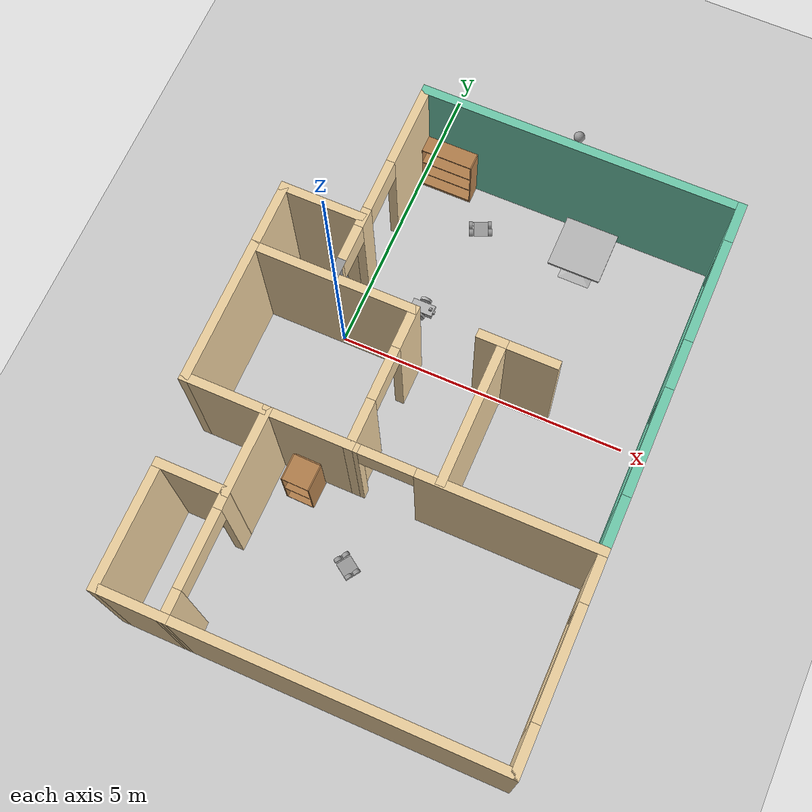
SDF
<sdf version="1.6">
 <world name="default">
  <plugin name="hello" filename="libhello.so"/>
  <light name="sun" type="directional">
   <pose>0 0 10 0 -0 0</pose>
   <diffuse>0.8 0.8 0.8 1</diffuse>
   <specular>0.2 0.2 0.2 1</specular>
   <attenuation>
    <range>1000</range>
    <constant>0.9</constant>
    <linear>0.01</linear>
    <quadratic>0.001</quadratic>
   </attenuation>
   <direction>-0.5 0.1 -0.9</direction>
  </light>
  <model name="ground_plane">
   <static>1</static>
   <link name="link">
    <collision name="collision">
     <geometry><plane><normal>0 0 1</normal><size>100 100</size></plane></geometry>
     <surface>
      <contact><collide_bitmask>65535</collide_bitmask></contact>
      <friction><ode><mu>100</mu><mu2>50</mu2></ode></friction>
     </surface>
    </collision>
    <visual name="visual">
     <cast_shadows>0</cast_shadows>
     <geometry><plane><normal>0 0 1</normal><size>100 100</size></plane></geometry>
     <material>
      <script><uri>file://media/materials/scripts/gazebo.material</uri><name>Gazebo/Grey</name></script>
     </material>
    </visual>
   </link>
  </model>
  <gravity>0 0 -9.8</gravity>
  <magnetic_field>6e-06 2.3e-05 -4.2e-05</magnetic_field>
  <atmosphere type="adiabatic"/>
  <physics name="default_physics" default="0" type="ode">
   <max_step_size>0.001</max_step_size>
   <real_time_factor>1</real_time_factor>
   <real_time_update_rate>1000</real_time_update_rate>
  </physics>
  <scene><ambient>0.4 0.4 0.4 1</ambient><background>0.7 0.7 0.7 1</background><shadows>1</shadows></scene>
  <audio><device>default</device></audio>
  <spherical_coordinates>
   <surface_model>EARTH_WGS84</surface_model>
   <latitude_deg>0</latitude_deg>
   <longitude_deg>0</longitude_deg>
   <elevation>0</elevation>
   <heading_deg>0</heading_deg>
  </spherical_coordinates>
  <model name="combined_model">
   <model name="apt_1br">
    <pose>0.440605 -1.37151 0 0 -0 0</pose>
    <link name="Wall_10">
     <collision name="Wall_10_Collision">
      <geometry><box><size>5.5 0.15 2.5</size></box></geometry>
      <pose>0 0 1.25 0 -0 0</pose>
     </collision>
     <visual name="Wall_10_Visual">
      <pose>0 0 1.25 0 -0 0</pose>
      <geometry><box><size>5.5 0.15 2.5</size></box></geometry>
      <material>
       <script><uri>file://media/materials/scripts/gazebo.material</uri><name>Gazebo/Grey</name></script>
       <ambient>0.921569 0.807843 0.615686 1</ambient>
      </material>
      <meta><layer>0</layer></meta>
     </visual>
     <pose>0.674919 -4.65002 0 0 -0 3.14159</pose>
    </link>
    <link name="Wall_21">
     <collision name="Wall_21_Collision">
      <geometry><box><size>1.5 0.15 2.5</size></box></geometry>
      <pose>0 0 1.25 0 -0 0</pose>
     </collision>
     <visual name="Wall_21_Visual">
      <pose>0 0 1.25 0 -0 0</pose>
      <geometry><box><size>1.5 0.15 2.5</size></box></geometry>
      <material>
       <script><uri>file://media/materials/scripts/gazebo.material</uri><name>Gazebo/Grey</name></script>
       <ambient>0.921569 0.807843 0.615686 1</ambient>
      </material>
      <meta><layer>0</layer></meta>
     </visual>
     <pose>-1.32508 1.04998 0 0 -0 3.14159</pose>
    </link>
    <link name="Wall_29">
     <pose>3.34992 1.67498 0 0 -0 -1.5708</pose>
     <visual name="Wall_29_Visual_0">
      <pose>-2.69448 0 1.25 0 -0 0</pose>
      <geometry><box><size>0.71105 0.15 2.5</size></box></geometry>
      <material>
       <script><uri>file://media/materials/scripts/gazebo.material</uri><name>Gazebo/Grey</name></script>
       <ambient>0.435294 0.796078 0.67451 1</ambient>
      </material>
      <meta><layer>0</layer></meta>
     </visual>
     <collision name="Wall_29_Collision_0">
      <geometry><box><size>0.71105 0.15 2.5</size></box></geometry>
      <pose>-2.69448 0 1.25 0 -0 0</pose>
     </collision>
     <visual name="Wall_29_Visual_1">
      <pose>0.355525 0 0.375 0 -0 0</pose>
      <geometry><box><size>5.38895 0.15 0.75</size></box></geometry>
      <material>
       <script><uri>file://media/materials/scripts/gazebo.material</uri><name>Gazebo/Grey</name></script>
       <ambient>0.435294 0.796078 0.67451 1</ambient>
      </material>
      <meta><layer>0</layer></meta>
     </visual>
     <collision name="Wall_29_Collision_1">
      <geometry><box><size>5.38895 0.15 0.75</size></box></geometry>
      <pose>0.355525 0 0.375 0 -0 0</pose>
     </collision>
     <visual name="Wall_29_Visual_2">
      <pose>-0.124805 0 1.625 0 -0 0</pose>
      <geometry><box><size>0.82829 0.15 1.75</size></box></geometry>
      <material>
       <script><uri>file://media/materials/scripts/gazebo.material</uri><name>Gazebo/Grey</name></script>
       <ambient>0.435294 0.796078 0.67451 1</ambient>
      </material>
      <meta><layer>0</layer></meta>
     </visual>
     <collision name="Wall_29_Collision_2">
      <geometry><box><size>0.82829 0.15 1.75</size></box></geometry>
      <pose>-0.124805 0 1.625 0 -0 0</pose>
     </collision>
     <visual name="Wall_29_Visual_3">
      <pose>2.56967 0 1.625 0 -0 0</pose>
      <geometry><box><size>0.96066 0.15 1.75</size></box></geometry>
      <material>
       <script><uri>file://media/materials/scripts/gazebo.material</uri><name>Gazebo/Grey</name></script>
       <ambient>0.435294 0.796078 0.67451 1</ambient>
      </material>
      <meta><layer>0</layer></meta>
     </visual>
     <collision name="Wall_29_Collision_3">
      <geometry><box><size>0.96066 0.15 1.75</size></box></geometry>
      <pose>2.56967 0 1.625 0 -0 0</pose>
     </collision>
     <visual name="Wall_29_Visual_4">
      <pose>-1.43895 0 2.225 0 -0 0</pose>
      <geometry><box><size>1.8 0.15 0.55</size></box></geometry>
      <material>
       <script><uri>file://media/materials/scripts/gazebo.material</uri><name>Gazebo/Grey</name></script>
       <ambient>0.435294 0.796078 0.67451 1</ambient>
      </material>
      <meta><layer>0</layer></meta>
     </visual>
     <collision name="Wall_29_Collision_4">
      <geometry><box><size>1.8 0.15 0.55</size></box></geometry>
      <pose>-1.43895 0 2.225 0 -0 0</pose>
     </collision>
     <visual name="Wall_29_Visual_5">
      <pose>1.18934 0 2.225 0 -0 0</pose>
      <geometry><box><size>1.8 0.15 0.55</size></box></geometry>
      <material>
       <script><uri>file://media/materials/scripts/gazebo.material</uri><name>Gazebo/Grey</name></script>
       <ambient>0.435294 0.796078 0.67451 1</ambient>
      </material>
      <meta><layer>0</layer></meta>
     </visual>
     <collision name="Wall_29_Collision_5">
      <geometry><box><size>1.8 0.15 0.55</size></box></geometry>
      <pose>1.18934 0 2.225 0 -0 0</pose>
     </collision>
    </link>
    <link name="Wall_31">
     <pose>3.34992 -2.97502 0 0 -0 1.5708</pose>
     <visual name="Wall_31_Visual_0">
      <pose>-1.34686 0 1.25 0 -0 0</pose>
      <geometry><box><size>0.806273 0.15 2.5</size></box></geometry>
      <material>
       <script><uri>file://media/materials/scripts/gazebo.material</uri><name>Gazebo/Grey</name></script>
       <ambient>0.921569 0.807843 0.615686 1</ambient>
      </material>
      <meta><layer>0</layer></meta>
     </visual>
     <collision name="Wall_31_Collision_0">
      <geometry><box><size>0.806273 0.15 2.5</size></box></geometry>
      <pose>-1.34686 0 1.25 0 -0 0</pose>
     </collision>
     <visual name="Wall_31_Visual_1">
      <pose>0.403136 0 0.375 0 -0 0</pose>
      <geometry><box><size>2.69373 0.15 0.75</size></box></geometry>
      <material>
       <script><uri>file://media/materials/scripts/gazebo.material</uri><name>Gazebo/Grey</name></script>
       <ambient>0.921569 0.807843 0.615686 1</ambient>
      </material>
      <meta><layer>0</layer></meta>
     </visual>
     <collision name="Wall_31_Collision_1">
      <geometry><box><size>2.69373 0.15 0.75</size></box></geometry>
      <pose>0.403136 0 0.375 0 -0 0</pose>
     </collision>
     <visual name="Wall_31_Visual_2">
      <pose>1.30314 0 1.625 0 -0 0</pose>
      <geometry><box><size>0.893727 0.15 1.75</size></box></geometry>
      <material>
       <script><uri>file://media/materials/scripts/gazebo.material</uri><name>Gazebo/Grey</name></script>
       <ambient>0.921569 0.807843 0.615686 1</ambient>
      </material>
      <meta><layer>0</layer></meta>
     </visual>
     <collision name="Wall_31_Collision_2">
      <geometry><box><size>0.893727 0.15 1.75</size></box></geometry>
      <pose>1.30314 0 1.625 0 -0 0</pose>
     </collision>
     <visual name="Wall_31_Visual_3">
      <pose>-0.043727 0 2.225 0 -0 0</pose>
      <geometry><box><size>1.8 0.15 0.55</size></box></geometry>
      <material>
       <script><uri>file://media/materials/scripts/gazebo.material</uri><name>Gazebo/Grey</name></script>
       <ambient>0.921569 0.807843 0.615686 1</ambient>
      </material>
      <meta><layer>0</layer></meta>
     </visual>
     <collision name="Wall_31_Collision_3">
      <geometry><box><size>1.8 0.15 0.55</size></box></geometry>
      <pose>-0.043727 0 2.225 0 -0 0</pose>
     </collision>
    </link>
    <link name="Wall_33">
     <pose>-0.650081 -0.125024 0 0 -0 -1.5708</pose>
     <visual name="Wall_33_Visual_0">
      <pose>-0.874194 0 1.25 0 -0 0</pose>
      <geometry><box><size>0.751611 0.15 2.5</size></box></geometry>
      <material>
       <script><uri>file://media/materials/scripts/gazebo.material</uri><name>Gazebo/Grey</name></script>
       <ambient>0.921569 0.807843 0.615686 1</ambient>
      </material>
      <meta><layer>0</layer></meta>
     </visual>
     <collision name="Wall_33_Collision_0">
      <geometry><box><size>0.751611 0.15 2.5</size></box></geometry>
      <pose>-0.874194 0 1.25 0 -0 0</pose>
     </collision>
     <visual name="Wall_33_Visual_1">
      <pose>0.825806 0 1.25 0 -0 0</pose>
      <geometry><box><size>0.848389 0.15 2.5</size></box></geometry>
      <material>
       <script><uri>file://media/materials/scripts/gazebo.material</uri><name>Gazebo/Grey</name></script>
       <ambient>0.921569 0.807843 0.615686 1</ambient>
      </material>
      <meta><layer>0</layer></meta>
     </visual>
     <collision name="Wall_33_Collision_1">
      <geometry><box><size>0.848389 0.15 2.5</size></box></geometry>
      <pose>0.825806 0 1.25 0 -0 0</pose>
     </collision>
     <visual name="Wall_33_Visual_2">
      <pose>-0.048389 0 2.25 0 -0 0</pose>
      <geometry><box><size>0.9 0.15 0.5</size></box></geometry>
      <material>
       <script><uri>file://media/materials/scripts/gazebo.material</uri><name>Gazebo/Grey</name></script>
       <ambient>0.921569 0.807843 0.615686 1</ambient>
      </material>
      <meta><layer>0</layer></meta>
     </visual>
     <collision name="Wall_33_Collision_2">
      <geometry><box><size>0.9 0.15 0.5</size></box></geometry>
      <pose>-0.048389 0 2.25 0 -0 0</pose>
     </collision>
    </link>
    <link name="Wall_34">
     <collision name="Wall_34_Collision">
      <geometry><box><size>1.5 0.15 2.5</size></box></geometry>
      <pose>0 0 1.25 0 -0 0</pose>
     </collision>
     <visual name="Wall_34_Visual">
      <pose>0 0 1.25 0 -0 0</pose>
      <geometry><box><size>1.5 0.15 2.5</size></box></geometry>
      <material>
       <script><uri>file://media/materials/scripts/gazebo.material</uri><name>Gazebo/Grey</name></script>
       <ambient>0.921569 0.807843 0.615686 1</ambient>
      </material>
      <meta><layer>0</layer></meta>
     </visual>
     <pose>-1.32508 -1.30002 0 0 -0 3.14159</pose>
    </link>
    <link name="Wall_36">
     <pose>1.34992 -1.30002 0 0 -0 0</pose>
     <visual name="Wall_36_Visual_0">
      <pose>-1.96133 0 1.25 0 -0 0</pose>
      <geometry><box><size>0.227341 0.15 2.5</size></box></geometry>
      <material>
       <script><uri>file://media/materials/scripts/gazebo.material</uri><name>Gazebo/Grey</name></script>
       <ambient>0.921569 0.807843 0.615686 1</ambient>
      </material>
      <meta><layer>0</layer></meta>
     </visual>
     <collision name="Wall_36_Collision_0">
      <geometry><box><size>0.227341 0.15 2.5</size></box></geometry>
      <pose>-1.96133 0 1.25 0 -0 0</pose>
     </collision>
     <visual name="Wall_36_Visual_1">
      <pose>0.56367 0 1.25 0 -0 0</pose>
      <geometry><box><size>3.02266 0.15 2.5</size></box></geometry>
      <material>
       <script><uri>file://media/materials/scripts/gazebo.material</uri><name>Gazebo/Grey</name></script>
       <ambient>0.921569 0.807843 0.615686 1</ambient>
      </material>
      <meta><layer>0</layer></meta>
     </visual>
     <collision name="Wall_36_Collision_1">
      <geometry><box><size>3.02266 0.15 2.5</size></box></geometry>
      <pose>0.56367 0 1.25 0 -0 0</pose>
     </collision>
     <visual name="Wall_36_Visual_2">
      <pose>-1.39766 0 2.25 0 -0 0</pose>
      <geometry><box><size>0.9 0.15 0.5</size></box></geometry>
      <material>
       <script><uri>file://media/materials/scripts/gazebo.material</uri><name>Gazebo/Grey</name></script>
       <ambient>0.921569 0.807843 0.615686 1</ambient>
      </material>
      <meta><layer>0</layer></meta>
     </visual>
     <collision name="Wall_36_Collision_2">
      <geometry><box><size>0.9 0.15 0.5</size></box></geometry>
      <pose>-1.39766 0 2.25 0 -0 0</pose>
     </collision>
    </link>
    <link name="Wall_38">
     <collision name="Wall_38_Collision">
      <geometry><box><size>2.5 0.15 2.5</size></box></geometry>
      <pose>0 0 1.25 0 -0 0</pose>
     </collision>
     <visual name="Wall_38_Visual">
      <pose>0 0 1.25 0 -0 0</pose>
      <geometry><box><size>2.5 0.15 2.5</size></box></geometry>
      <material>
       <script><uri>file://media/materials/scripts/gazebo.material</uri><name>Gazebo/Grey</name></script>
       <ambient>0.921569 0.807843 0.615686 1</ambient>
      </material>
      <meta><layer>0</layer></meta>
     </visual>
     <pose>0.806186 -0.096149 0 0 -0 1.5708</pose>
    </link>
    <link name="Wall_41">
     <collision name="Wall_41_Collision">
      <geometry><box><size>1 0.15 2.5</size></box></geometry>
      <pose>0 0 1.25 0 -0 0</pose>
     </collision>
     <visual name="Wall_41_Visual">
      <pose>0 0 1.25 0 -0 0</pose>
      <geometry><box><size>1 0.15 2.5</size></box></geometry>
      <material>
       <script><uri>file://media/materials/scripts/gazebo.material</uri><name>Gazebo/Grey</name></script>
       <ambient>0.921569 0.807843 0.615686 1</ambient>
      </material>
      <meta><layer>0</layer></meta>
     </visual>
     <pose>1.23119 1.07885 0 0 -0 0</pose>
    </link>
    <link name="Wall_43">
     <collision name="Wall_43_Collision">
      <geometry><box><size>0.5 0.15 2.5</size></box></geometry>
      <pose>0 0 1.25 0 -0 0</pose>
     </collision>
     <visual name="Wall_43_Visual">
      <pose>0 0 1.25 0 -0 0</pose>
      <geometry><box><size>0.5 0.15 2.5</size></box></geometry>
      <material>
       <script><uri>file://media/materials/scripts/gazebo.material</uri><name>Gazebo/Grey</name></script>
       <ambient>0.921569 0.807843 0.615686 1</ambient>
      </material>
      <meta><layer>0</layer></meta>
     </visual>
     <pose>0.631186 1.07885 0 0 -0 3.14159</pose>
    </link>
    <link name="Wall_5">
     <pose>-2.00008 2.96898 0 0 -0 1.5708</pose>
     <visual name="Wall_5_Visual_0">
      <pose>-1.71167 0 1.25 0 -0 0</pose>
      <geometry><box><size>0.064664 0.15 2.5</size></box></geometry>
      <material>
       <script><uri>file://media/materials/scripts/gazebo.material</uri><name>Gazebo/Grey</name></script>
       <ambient>0.921569 0.807843 0.615686 1</ambient>
      </material>
      <meta><layer>0</layer></meta>
     </visual>
     <collision name="Wall_5_Collision_0">
      <geometry><box><size>0.064664 0.15 2.5</size></box></geometry>
      <pose>-1.71167 0 1.25 0 -0 0</pose>
     </collision>
     <visual name="Wall_5_Visual_1">
      <pose>-0.81386 0 1.25 0 -0 0</pose>
      <geometry><box><size>0.330951 0.15 2.5</size></box></geometry>
      <material>
       <script><uri>file://media/materials/scripts/gazebo.material</uri><name>Gazebo/Grey</name></script>
       <ambient>0.921569 0.807843 0.615686 1</ambient>
      </material>
      <meta><layer>0</layer></meta>
     </visual>
     <collision name="Wall_5_Collision_1">
      <geometry><box><size>0.330951 0.15 2.5</size></box></geometry>
      <pose>-0.81386 0 1.25 0 -0 0</pose>
     </collision>
     <visual name="Wall_5_Visual_2">
      <pose>0.997808 0 1.25 0 -0 0</pose>
      <geometry><box><size>1.49239 0.15 2.5</size></box></geometry>
      <material>
       <script><uri>file://media/materials/scripts/gazebo.material</uri><name>Gazebo/Grey</name></script>
       <ambient>0.921569 0.807843 0.615686 1</ambient>
      </material>
      <meta><layer>0</layer></meta>
     </visual>
     <collision name="Wall_5_Collision_2">
      <geometry><box><size>1.49239 0.15 2.5</size></box></geometry>
      <pose>0.997808 0 1.25 0 -0 0</pose>
     </collision>
     <visual name="Wall_5_Visual_3">
      <pose>-1.32934 0 2.25 0 -0 0</pose>
      <geometry><box><size>0.7 0.15 0.5</size></box></geometry>
      <material>
       <script><uri>file://media/materials/scripts/gazebo.material</uri><name>Gazebo/Grey</name></script>
       <ambient>0.921569 0.807843 0.615686 1</ambient>
      </material>
      <meta><layer>0</layer></meta>
     </visual>
     <collision name="Wall_5_Collision_3">
      <geometry><box><size>0.7 0.15 0.5</size></box></geometry>
      <pose>-1.32934 0 2.25 0 -0 0</pose>
     </collision>
     <visual name="Wall_5_Visual_4">
      <pose>-0.198385 0 2.25 0 -0 0</pose>
      <geometry><box><size>0.9 0.15 0.5</size></box></geometry>
      <material>
       <script><uri>file://media/materials/scripts/gazebo.material</uri><name>Gazebo/Grey</name></script>
       <ambient>0.921569 0.807843 0.615686 1</ambient>
      </material>
      <meta><layer>0</layer></meta>
     </visual>
     <collision name="Wall_5_Collision_4">
      <geometry><box><size>0.9 0.15 0.5</size></box></geometry>
      <pose>-0.198385 0 2.25 0 -0 0</pose>
     </collision>
    </link>
    <link name="Wall_54">
     <collision name="Wall_54_Collision">
      <geometry><box><size>1.5 0.15 2.5</size></box></geometry>
      <pose>0 0 1.25 0 -0 0</pose>
     </collision>
     <visual name="Wall_54_Visual">
      <pose>0 0 1.25 0 -0 0</pose>
      <geometry><box><size>1.5 0.15 2.5</size></box></geometry>
      <material>
       <script><uri>file://media/materials/scripts/gazebo.material</uri><name>Gazebo/Grey</name></script>
       <ambient>0.921569 0.807843 0.615686 1</ambient>
      </material>
      <meta><layer>0</layer></meta>
     </visual>
     <pose>-2.67508 1.04998 0 0 -0 3.14159</pose>
    </link>
    <link name="Wall_55">
     <collision name="Wall_55_Collision">
      <geometry><box><size>2.5 0.15 2.5</size></box></geometry>
      <pose>0 0 1.25 0 -0 0</pose>
     </collision>
     <visual name="Wall_55_Visual">
      <pose>0 0 1.25 0 -0 0</pose>
      <geometry><box><size>2.5 0.15 2.5</size></box></geometry>
      <material>
       <script><uri>file://media/materials/scripts/gazebo.material</uri><name>Gazebo/Grey</name></script>
       <ambient>0.921569 0.807843 0.615686 1</ambient>
      </material>
      <meta><layer>0</layer></meta>
     </visual>
     <pose>-3.35008 -0.125024 0 0 -0 -1.5708</pose>
    </link>
    <link name="Wall_56">
     <collision name="Wall_56_Collision">
      <geometry><box><size>1.5 0.15 2.5</size></box></geometry>
      <pose>0 0 1.25 0 -0 0</pose>
     </collision>
     <visual name="Wall_56_Visual">
      <pose>0 0 1.25 0 -0 0</pose>
      <geometry><box><size>1.5 0.15 2.5</size></box></geometry>
      <material>
       <script><uri>file://media/materials/scripts/gazebo.material</uri><name>Gazebo/Grey</name></script>
       <ambient>0.921569 0.807843 0.615686 1</ambient>
      </material>
      <meta><layer>0</layer></meta>
     </visual>
     <pose>-2.67508 -1.30002 0 0 -0 0</pose>
    </link>
    <link name="Wall_57">
     <collision name="Wall_57_Collision">
      <geometry><box><size>1.5 0.15 2.5</size></box></geometry>
      <pose>0 0 1.25 0 -0 0</pose>
     </collision>
     <visual name="Wall_57_Visual">
      <pose>0 0 1.25 0 -0 0</pose>
      <geometry><box><size>1.5 0.15 2.5</size></box></geometry>
      <material>
       <script><uri>file://media/materials/scripts/gazebo.material</uri><name>Gazebo/Grey</name></script>
       <ambient>0.921569 0.807843 0.615686 1</ambient>
      </material>
      <meta><layer>0</layer></meta>
     </visual>
     <pose>-2.0017 -1.97502 0 0 -0 -1.57319</pose>
    </link>
    <link name="Wall_58">
     <collision name="Wall_58_Collision">
      <geometry><box><size>1.247 0.15 2.5</size></box></geometry>
      <pose>0 0 1.25 0 -0 0</pose>
     </collision>
     <visual name="Wall_58_Visual">
      <pose>0 0 1.25 0 -0 0</pose>
      <geometry><box><size>1.247 0.15 2.5</size></box></geometry>
      <material>
       <script><uri>file://media/materials/scripts/gazebo.material</uri><name>Gazebo/Grey</name></script>
       <ambient>0.921569 0.807843 0.615686 1</ambient>
      </material>
      <meta><layer>0</layer></meta>
     </visual>
     <pose>-2.55181 -2.65002 0 0 -0 3.14159</pose>
    </link>
    <link name="Wall_6">
     <collision name="Wall_6_Collision">
      <geometry><box><size>5.5 0.15 2.5</size></box></geometry>
      <pose>0 0 1.25 0 -0 0</pose>
     </collision>
     <visual name="Wall_6_Visual">
      <pose>0 0 1.25 0 -0 0</pose>
      <geometry><box><size>5.5 0.15 2.5</size></box></geometry>
      <material>
       <script><uri>file://media/materials/scripts/gazebo.material</uri><name>Gazebo/Grey</name></script>
       <ambient>0.435294 0.796078 0.67451 1</ambient>
      </material>
      <meta><layer>0</layer></meta>
     </visual>
     <pose>0.674919 4.64398 0 0 -0 0.002243</pose>
    </link>
    <link name="Wall_62">
     <collision name="Wall_62_Collision">
      <geometry><box><size>1.25 0.15 2.5</size></box></geometry>
      <pose>0 0 1.25 0 -0 0</pose>
     </collision>
     <visual name="Wall_62_Visual">
      <pose>0 0 1.25 0 -0 0</pose>
      <geometry><box><size>1.25 0.15 2.5</size></box></geometry>
      <material>
       <script><uri>file://media/materials/scripts/gazebo.material</uri><name>Gazebo/Grey</name></script>
       <ambient>0.921569 0.807843 0.615686 1</ambient>
      </material>
      <meta><layer>0</layer></meta>
     </visual>
     <pose>-2.55008 -4.65002 0 0 -0 3.14159</pose>
    </link>
    <link name="Wall_63">
     <collision name="Wall_63_Collision">
      <geometry><box><size>2 0.15 2.5</size></box></geometry>
      <pose>0 0 1.25 0 -0 0</pose>
     </collision>
     <visual name="Wall_63_Visual">
      <pose>0 0 1.25 0 -0 0</pose>
      <geometry><box><size>2 0.15 2.5</size></box></geometry>
      <material>
       <script><uri>file://media/materials/scripts/gazebo.material</uri><name>Gazebo/Grey</name></script>
       <ambient>0.921569 0.807843 0.615686 1</ambient>
      </material>
      <meta><layer>0</layer></meta>
     </visual>
     <pose>-3.10008 -3.72502 0 0 -0 1.5708</pose>
    </link>
    <link name="Wall_65">
     <pose>-2.0017 -3.65002 0 0 -0 -1.56918</pose>
     <visual name="Wall_65_Visual_0">
      <pose>-0.895757 0 1.25 0 -0 0</pose>
      <geometry><box><size>0.358489 0.15 2.5</size></box></geometry>
      <material>
       <script><uri>file://media/materials/scripts/gazebo.material</uri><name>Gazebo/Grey</name></script>
       <ambient>0.921569 0.807843 0.615686 1</ambient>
      </material>
      <meta><layer>0</layer></meta>
     </visual>
     <collision name="Wall_65_Collision_0">
      <geometry><box><size>0.358489 0.15 2.5</size></box></geometry>
      <pose>-0.895757 0 1.25 0 -0 0</pose>
     </collision>
     <visual name="Wall_65_Visual_1">
      <pose>0.815925 0 1.25 0 -0 0</pose>
      <geometry><box><size>0.518152 0.15 2.5</size></box></geometry>
      <material>
       <script><uri>file://media/materials/scripts/gazebo.material</uri><name>Gazebo/Grey</name></script>
       <ambient>0.921569 0.807843 0.615686 1</ambient>
      </material>
      <meta><layer>0</layer></meta>
     </visual>
     <collision name="Wall_65_Collision_1">
      <geometry><box><size>0.518152 0.15 2.5</size></box></geometry>
      <pose>0.815925 0 1.25 0 -0 0</pose>
     </collision>
     <visual name="Wall_65_Visual_2">
      <pose>-0.079832 0 2.25 0 -0 0</pose>
      <geometry><box><size>1.27336 0.15 0.5</size></box></geometry>
      <material>
       <script><uri>file://media/materials/scripts/gazebo.material</uri><name>Gazebo/Grey</name></script>
       <ambient>0.921569 0.807843 0.615686 1</ambient>
      </material>
      <meta><layer>0</layer></meta>
     </visual>
     <collision name="Wall_65_Collision_2">
      <geometry><box><size>1.27336 0.15 0.5</size></box></geometry>
      <pose>-0.079832 0 2.25 0 -0 0</pose>
     </collision>
    </link>
    <link name="Wall_70">
     <collision name="Wall_70_Collision">
      <geometry><box><size>1.25 0.15 2.5</size></box></geometry>
      <pose>0 0 1.25 0 -0 0</pose>
     </collision>
     <visual name="Wall_70_Visual">
      <pose>0 0 1.25 0 -0 0</pose>
      <geometry><box><size>1.25 0.15 2.5</size></box></geometry>
      <material>
       <script><uri>file://media/materials/scripts/gazebo.material</uri><name>Gazebo/Grey</name></script>
       <ambient>0.921569 0.807843 0.615686 1</ambient>
      </material>
      <meta><layer>0</layer></meta>
     </visual>
     <pose>-3.35008 1.59998 0 0 -0 1.5708</pose>
    </link>
    <link name="Wall_71">
     <collision name="Wall_71_Collision">
      <geometry><box><size>1.5 0.15 2.5</size></box></geometry>
      <pose>0 0 1.25 0 -0 0</pose>
     </collision>
     <visual name="Wall_71_Visual">
      <pose>0 0 1.25 0 -0 0</pose>
      <geometry><box><size>1.5 0.15 2.5</size></box></geometry>
      <material>
       <script><uri>file://media/materials/scripts/gazebo.material</uri><name>Gazebo/Grey</name></script>
       <ambient>0.921569 0.807843 0.615686 1</ambient>
      </material>
      <meta><layer>0</layer></meta>
     </visual>
     <pose>-2.67508 2.14998 0 0 -0 0</pose>
    </link>
    <link name="Wall_73">
     <collision name="Wall_73_Collision">
      <geometry><box><size>0.4 0.15 2.5</size></box></geometry>
      <pose>0 0 1.25 0 -0 0</pose>
     </collision>
     <visual name="Wall_73_Visual">
      <pose>0 0 1.25 0 -0 0</pose>
      <geometry><box><size>0.4 0.15 2.5</size></box></geometry>
      <material>
       <script><uri>file://media/materials/scripts/gazebo.material</uri><name>Gazebo/Grey</name></script>
       <ambient>1 1 1 1</ambient>
      </material>
      <meta><layer>0</layer></meta>
     </visual>
     <pose>-2.00008 1.17498 0 0 -0 1.5708</pose>
    </link>
    <static>1</static>
   </model>
   <model name="bookshelf">
    <static>1</static>
    <link name="link">
     <inertial><mass>1</mass></inertial>
     <collision name="back">
      <pose>0 0.005 0.6 0 -0 0</pose>
      <geometry><box><size>0.9 0.01 1.2</size></box></geometry>
     </collision>
     <visual name="visual1">
      <pose>0 0.005 0.6 0 -0 0</pose>
      <geometry><box><size>0.9 0.01 1.2</size></box></geometry>
      <material>
       <script><uri>file://media/materials/scripts/gazebo.material</uri><name>Gazebo/Wood</name></script>
      </material>
     </visual>
     <collision name="left_side">
      <pose>0.45 -0.195 0.6 0 -0 0</pose>
      <geometry><box><size>0.02 0.4 1.2</size></box></geometry>
     </collision>
     <visual name="visual2">
      <pose>0.45 -0.195 0.6 0 -0 0</pose>
      <geometry><box><size>0.02 0.4 1.2</size></box></geometry>
      <material>
       <script><uri>file://media/materials/scripts/gazebo.material</uri><name>Gazebo/Wood</name></script>
      </material>
     </visual>
     <collision name="right_side">
      <pose>-0.45 -0.195 0.6 0 -0 0</pose>
      <geometry><box><size>0.02 0.4 1.2</size></box></geometry>
     </collision>
     <visual name="visual3">
      <pose>-0.45 -0.195 0.6 0 -0 0</pose>
      <geometry><box><size>0.02 0.4 1.2</size></box></geometry>
      <material>
       <script><uri>file://media/materials/scripts/gazebo.material</uri><name>Gazebo/Wood</name></script>
      </material>
     </visual>
     <collision name="bottom">
      <pose>0 -0.195 0.03 0 -0 0</pose>
      <geometry><box><size>0.88 0.4 0.06</size></box></geometry>
     </collision>
     <visual name="visual4">
      <pose>0 -0.195 0.03 0 -0 0</pose>
      <geometry><box><size>0.88 0.4 0.06</size></box></geometry>
      <material>
       <script><uri>file://media/materials/scripts/gazebo.material</uri><name>Gazebo/Wood</name></script>
      </material>
     </visual>
     <collision name="top">
      <pose>0 -0.195 1.19 0 -0 0</pose>
      <geometry><box><size>0.88 0.4 0.02</size></box></geometry>
     </collision>
     <visual name="visual5">
      <pose>0 -0.195 1.19 0 -0 0</pose>
      <geometry><box><size>0.88 0.4 0.02</size></box></geometry>
      <material>
       <script><uri>file://media/materials/scripts/gazebo.material</uri><name>Gazebo/Wood</name></script>
      </material>
     </visual>
     <collision name="low_shelf">
      <pose>0 -0.195 0.43 0 -0 0</pose>
      <geometry><box><size>0.88 0.4 0.02</size></box></geometry>
     </collision>
     <visual name="visual6">
      <pose>0 -0.195 0.43 0 -0 0</pose>
      <geometry><box><size>0.88 0.4 0.02</size></box></geometry>
      <material>
       <script><uri>file://media/materials/scripts/gazebo.material</uri><name>Gazebo/Wood</name></script>
      </material>
     </visual>
     <collision name="high_shelf">
      <pose>0 -0.195 0.8 0 -0 0</pose>
      <geometry><box><size>0.88 0.4 0.02</size></box></geometry>
     </collision>
     <visual name="visual7">
      <pose>0 -0.195 0.8 0 -0 0</pose>
      <geometry><box><size>0.88 0.4 0.02</size></box></geometry>
      <material>
       <script><uri>file://media/materials/scripts/gazebo.material</uri><name>Gazebo/Wood</name></script>
      </material>
     </visual>
    </link>
    <pose>-1.04171 3.29108 0 0 -0 0</pose>
   </model>
   <model name="cabinet">
    <static>1</static>
    <link name="cabinet_bottom_plate">
     <inertial>
      <pose>0 0 -1 0 -0 0</pose>
      <inertia><ixx>2.05</ixx><ixy>0</ixy><ixz>0</ixz><iyy>2.05</iyy><iyz>0</iyz><izz>2.05</izz></inertia>
      <mass>25</mass>
     </inertial>
     <collision name="cabinet_bottom_plate_geom">
      <pose>0 0 0.01 0 -0 0</pose>
      <geometry><box><size>0.45 0.45 0.02</size></box></geometry>
     </collision>
     <visual name="cabinet_bottom_plate_geom_visual">
      <pose>0 0 0.01 0 -0 0</pose>
      <geometry><box><size>0.45 0.45 0.02</size></box></geometry>
      <material>
       <script><uri>file://media/materials/scripts/gazebo.material</uri><name>Gazebo/Wood</name></script>
      </material>
     </visual>
     <collision name="cabinet_bottom_plate_geom_cabinet_back_plate">
      <pose>0.235 0 0.51 0 -0 0</pose>
      <geometry><box><size>0.02 0.45 1.02</size></box></geometry>
     </collision>
     <visual name="cabinet_bottom_plate_geom_cabinet_back_plate_visual">
      <pose>0.235 0 0.51 0 -0 0</pose>
      <geometry><box><size>0.02 0.45 1.02</size></box></geometry>
      <material>
       <script><uri>file://media/materials/scripts/gazebo.material</uri><name>Gazebo/Wood</name></script>
      </material>
     </visual>
     <collision name="cabinet_bottom_plate_geom_cabinet_left_plate">
      <pose>0 0.235 0.51 0 -0 0</pose>
      <geometry><box><size>0.45 0.02 1.02</size></box></geometry>
     </collision>
     <visual name="cabinet_bottom_plate_geom_cabinet_left_plate_visual">
      <pose>0 0.235 0.51 0 -0 0</pose>
      <geometry><box><size>0.45 0.02 1.02</size></box></geometry>
      <material>
       <script><uri>file://media/materials/scripts/gazebo.material</uri><name>Gazebo/Wood</name></script>
      </material>
     </visual>
     <collision name="cabinet_bottom_plate_geom_cabinet_middle_plate">
      <pose>0 0 0.51 0 -0 0</pose>
      <geometry><box><size>0.45 0.45 0.02</size></box></geometry>
     </collision>
     <visual name="cabinet_bottom_plate_geom_cabinet_middle_plate_visual">
      <pose>0 0 0.51 0 -0 0</pose>
      <geometry><box><size>0.45 0.45 0.02</size></box></geometry>
      <material>
       <script><uri>file://media/materials/scripts/gazebo.material</uri><name>Gazebo/Wood</name></script>
      </material>
     </visual>
     <collision name="cabinet_bottom_plate_geom_cabinet_right_plate">
      <pose>0 -0.235 0.51 0 -0 0</pose>
      <geometry><box><size>0.45 0.02 1.02</size></box></geometry>
     </collision>
     <visual name="cabinet_bottom_plate_geom_cabinet_right_plate_visual">
      <pose>0 -0.235 0.51 0 -0 0</pose>
      <geometry><box><size>0.45 0.02 1.02</size></box></geometry>
      <material>
       <script><uri>file://media/materials/scripts/gazebo.material</uri><name>Gazebo/Wood</name></script>
      </material>
     </visual>
     <collision name="cabinet_bottom_plate_geom_cabinet_top_plate">
      <pose>0 0 1.01 0 -0 0</pose>
      <geometry><box><size>0.45 0.45 0.02</size></box></geometry>
     </collision>
     <visual name="cabinet_bottom_plate_geom_cabinet_top_plate_visual">
      <pose>0 0 1.01 0 -0 0</pose>
      <geometry><box><size>0.45 0.45 0.02</size></box></geometry>
      <material>
       <script><uri>file://media/materials/scripts/gazebo.material</uri><name>Gazebo/Wood</name></script>
      </material>
     </visual>
    </link>
    <pose>-0.989306 -2.99197 0 0 -0 1.55199</pose>
   </model>
   <model name="cafe_table">
    <static>1</static>
    <link name="link">
     <collision name="surface">
      <pose>0 0 0.755 0 -0 0</pose>
      <geometry><box><size>0.913 0.913 0.04</size></box></geometry>
     </collision>
     <collision name="column">
      <pose>0 0 0.37 0 -0 0</pose>
      <geometry><box><size>0.042 0.042 0.74</size></box></geometry>
     </collision>
     <collision name="base">
      <pose>0 0 0.02 0 -0 0</pose>
      <geometry><box><size>0.56 0.56 0.04</size></box></geometry>
     </collision>
     <visual name="visual">
      <geometry><mesh><uri>model://cafe_table/meshes/cafe_table.dae</uri></mesh></geometry>
     </visual>
    </link>
    <pose>1.64758 2.46156 0 0 -0 0</pose>
   </model>
   <model name="fwd_robot">
    <link name="link_4_clone">
     <inertial>
      <mass>1</mass>
      <inertia><ixx>0.145833</ixx><ixy>0</ixy><ixz>0</ixz><iyy>0.145833</iyy><iyz>0</iyz><izz>0.125</izz></inertia>
     </inertial>
     <pose>-0.072 -0.1635 -0 1.5708 -0 0</pose>
     <visual name="visual">
      <geometry><cylinder><radius>0.065</radius><length>0.065</length></cylinder></geometry>
      <material>
       <lighting>1</lighting>
       <script><uri>file://media/materials/scripts/gazebo.material</uri><name>Gazebo/Grey</name></script>
       <shader type="vertex"><normal_map>__default__</normal_map></shader>
       <ambient>0.3 0.3 0.3 1</ambient>
       <diffuse>0.7 0.7 0.7 1</diffuse>
       <specular>0.01 0.01 0.01 1</specular>
       <emissive>0 0 0 1</emissive>
      </material>
     </visual>
     <collision name="collision">
      <geometry><cylinder><radius>0.065</radius><length>0.065</length></cylinder></geometry>
      <surface>
       <friction>
        <ode><mu>1</mu><mu2>1</mu2><fdir1>0 0 0</fdir1><slip1>0</slip1><slip2>0</slip2></ode>
        <torsional>
         <coefficient>1</coefficient>
         <patch_radius>0</patch_radius>
         <surface_radius>0</surface_radius>
         <use_patch_radius>1</use_patch_radius>
         <ode><slip>0</slip></ode>
        </torsional>
       </friction>
       <bounce><restitution_coefficient>0</restitution_coefficient><threshold>1e+06</threshold></bounce>
       <contact>
        <collide_without_contact>0</collide_without_contact>
        <collide_without_contact_bitmask>1</collide_without_contact_bitmask>
        <collide_bitmask>1</collide_bitmask>
        <ode>
         <soft_cfm>0</soft_cfm>
         <soft_erp>0.2</soft_erp>
         <kp>1e+13</kp>
         <kd>1</kd>
         <max_vel>0.01</max_vel>
         <min_depth>0</min_depth>
        </ode>
        <bullet>
         <split_impulse>1</split_impulse>
         <split_impulse_penetration_threshold>-0.01</split_impulse_penetration_threshold>
         <soft_cfm>0</soft_cfm>
         <soft_erp>0.2</soft_erp>
         <kp>1e+13</kp>
         <kd>1</kd>
        </bullet>
       </contact>
      </surface>
     </collision>
    </link>
    <link name="link_4_clone_0">
     <inertial>
      <mass>1</mass>
      <inertia><ixx>0.145833</ixx><ixy>0</ixy><ixz>0</ixz><iyy>0.145833</iyy><iyz>0</iyz><izz>0.125</izz></inertia>
     </inertial>
     <pose>0.073 -0.1635 -0 1.5708 -0 0</pose>
     <visual name="visual">
      <geometry><cylinder><radius>0.065</radius><length>0.065</length></cylinder></geometry>
      <material>
       <lighting>1</lighting>
       <script><uri>file://media/materials/scripts/gazebo.material</uri><name>Gazebo/Grey</name></script>
       <shader type="vertex"><normal_map>__default__</normal_map></shader>
       <ambient>0.3 0.3 0.3 1</ambient>
       <diffuse>0.7 0.7 0.7 1</diffuse>
       <specular>0.01 0.01 0.01 1</specular>
       <emissive>0 0 0 1</emissive>
      </material>
     </visual>
     <collision name="collision">
      <geometry><cylinder><radius>0.065</radius><length>0.065</length></cylinder></geometry>
      <surface>
       <friction>
        <ode><mu>1</mu><mu2>1</mu2><fdir1>0 0 0</fdir1><slip1>0</slip1><slip2>0</slip2></ode>
        <torsional>
         <coefficient>1</coefficient>
         <patch_radius>0</patch_radius>
         <surface_radius>0</surface_radius>
         <use_patch_radius>1</use_patch_radius>
         <ode><slip>0</slip></ode>
        </torsional>
       </friction>
       <bounce><restitution_coefficient>0</restitution_coefficient><threshold>1e+06</threshold></bounce>
       <contact>
        <collide_without_contact>0</collide_without_contact>
        <collide_without_contact_bitmask>1</collide_without_contact_bitmask>
        <collide_bitmask>1</collide_bitmask>
        <ode>
         <soft_cfm>0</soft_cfm>
         <soft_erp>0.2</soft_erp>
         <kp>1e+13</kp>
         <kd>1</kd>
         <max_vel>0.01</max_vel>
         <min_depth>0</min_depth>
        </ode>
        <bullet>
         <split_impulse>1</split_impulse>
         <split_impulse_penetration_threshold>-0.01</split_impulse_penetration_threshold>
         <soft_cfm>0</soft_cfm>
         <soft_erp>0.2</soft_erp>
         <kp>1e+13</kp>
         <kd>1</kd>
        </bullet>
       </contact>
      </surface>
     </collision>
    </link>
    <link name="link_4_clone_0_clone">
     <inertial>
      <mass>1</mass>
      <inertia><ixx>0.145833</ixx><ixy>0</ixy><ixz>0</ixz><iyy>0.145833</iyy><iyz>0</iyz><izz>0.125</izz></inertia>
      <pose>0 0 0 -0.01 0 0</pose>
     </inertial>
     <pose>0.073 0.1665 -0 -1.5708 0 0</pose>
     <visual name="visual">
      <geometry><cylinder><radius>0.065</radius><length>0.065</length></cylinder></geometry>
      <material>
       <lighting>1</lighting>
       <script><uri>file://media/materials/scripts/gazebo.material</uri><name>Gazebo/Grey</name></script>
       <shader type="vertex"><normal_map>__default__</normal_map></shader>
       <ambient>0.3 0.3 0.3 1</ambient>
       <diffuse>0.7 0.7 0.7 1</diffuse>
       <specular>0.01 0.01 0.01 1</specular>
       <emissive>0 0 0 1</emissive>
      </material>
     </visual>
     <collision name="collision">
      <geometry><cylinder><radius>0.065</radius><length>0.065</length></cylinder></geometry>
      <surface>
       <friction>
        <ode><mu>1</mu><mu2>1</mu2><fdir1>0 0 0</fdir1><slip1>0</slip1><slip2>0</slip2></ode>
        <torsional>
         <coefficient>1</coefficient>
         <patch_radius>0</patch_radius>
         <surface_radius>0</surface_radius>
         <use_patch_radius>1</use_patch_radius>
         <ode><slip>0</slip></ode>
        </torsional>
       </friction>
       <bounce><restitution_coefficient>0</restitution_coefficient><threshold>1e+06</threshold></bounce>
       <contact>
        <collide_without_contact>0</collide_without_contact>
        <collide_without_contact_bitmask>1</collide_without_contact_bitmask>
        <collide_bitmask>1</collide_bitmask>
        <ode>
         <soft_cfm>0</soft_cfm>
         <soft_erp>0.2</soft_erp>
         <kp>1e+13</kp>
         <kd>1</kd>
         <max_vel>0.01</max_vel>
         <min_depth>0</min_depth>
        </ode>
        <bullet>
         <split_impulse>1</split_impulse>
         <split_impulse_penetration_threshold>-0.01</split_impulse_penetration_threshold>
         <soft_cfm>0</soft_cfm>
         <soft_erp>0.2</soft_erp>
         <kp>1e+13</kp>
         <kd>1</kd>
        </bullet>
       </contact>
      </surface>
     </collision>
    </link>
    <link name="link_4_clone_1">
     <inertial>
      <mass>1</mass>
      <inertia><ixx>0.145833</ixx><ixy>0</ixy><ixz>0</ixz><iyy>0.145833</iyy><iyz>0</iyz><izz>0.125</izz></inertia>
     </inertial>
     <pose>-0.072 0.1665 -0 -1.5708 0 0</pose>
     <visual name="visual">
      <geometry><cylinder><radius>0.065</radius><length>0.065</length></cylinder></geometry>
      <material>
       <lighting>1</lighting>
       <script><uri>file://media/materials/scripts/gazebo.material</uri><name>Gazebo/Grey</name></script>
       <shader type="vertex"><normal_map>__default__</normal_map></shader>
       <ambient>0.3 0.3 0.3 1</ambient>
       <diffuse>0.7 0.7 0.7 1</diffuse>
       <specular>0.01 0.01 0.01 1</specular>
       <emissive>0 0 0 1</emissive>
      </material>
     </visual>
     <collision name="collision">
      <geometry><cylinder><radius>0.065</radius><length>0.065</length></cylinder></geometry>
      <surface>
       <friction>
        <ode><mu>1</mu><mu2>1</mu2><fdir1>0 0 0</fdir1><slip1>0</slip1><slip2>0</slip2></ode>
        <torsional>
         <coefficient>1</coefficient>
         <patch_radius>0</patch_radius>
         <surface_radius>0</surface_radius>
         <use_patch_radius>1</use_patch_radius>
         <ode><slip>0</slip></ode>
        </torsional>
       </friction>
       <bounce><restitution_coefficient>0</restitution_coefficient><threshold>1e+06</threshold></bounce>
       <contact>
        <collide_without_contact>0</collide_without_contact>
        <collide_without_contact_bitmask>1</collide_without_contact_bitmask>
        <collide_bitmask>1</collide_bitmask>
        <ode>
         <soft_cfm>0</soft_cfm>
         <soft_erp>0.2</soft_erp>
         <kp>1e+13</kp>
         <kd>1</kd>
         <max_vel>0.01</max_vel>
         <min_depth>0</min_depth>
        </ode>
        <bullet>
         <split_impulse>1</split_impulse>
         <split_impulse_penetration_threshold>-0.01</split_impulse_penetration_threshold>
         <soft_cfm>0</soft_cfm>
         <soft_erp>0.2</soft_erp>
         <kp>1e+13</kp>
         <kd>1</kd>
        </bullet>
       </contact>
      </surface>
     </collision>
    </link>
    <link name="link_5">
     <inertial>
      <mass>1</mass>
      <inertia>
       <ixx>0.166667</ixx>
       <ixy>0</ixy>
       <ixz>0</ixz>
       <iyy>0.166667</iyy>
       <iyz>0</iyz>
       <izz>0.166667</izz>
      </inertia>
     </inertial>
     <pose>-0.002 -0.006 -0 0 -0 0</pose>
     <visual name="visual">
      <geometry><box><size>0.27 0.25 0.00635</size></box></geometry>
      <material>
       <lighting>1</lighting>
       <script><uri>file://media/materials/scripts/gazebo.material</uri><name>Gazebo/Grey</name></script>
       <shader type="vertex"><normal_map>__default__</normal_map></shader>
       <ambient>0.3 0.3 0.3 1</ambient>
       <diffuse>0.7 0.7 0.7 1</diffuse>
       <specular>0.01 0.01 0.01 1</specular>
       <emissive>0 0 0 1</emissive>
      </material>
     </visual>
     <collision name="collision">
      <geometry><box><size>0.27 0.25 0.00635</size></box></geometry>
      <surface>
       <friction>
        <ode><mu>1</mu><mu2>1</mu2><fdir1>0 0 0</fdir1><slip1>0</slip1><slip2>0</slip2></ode>
        <torsional>
         <coefficient>1</coefficient>
         <patch_radius>0</patch_radius>
         <surface_radius>0</surface_radius>
         <use_patch_radius>1</use_patch_radius>
         <ode><slip>0</slip></ode>
        </torsional>
       </friction>
       <bounce><restitution_coefficient>0</restitution_coefficient><threshold>1e+06</threshold></bounce>
       <contact>
        <collide_without_contact>0</collide_without_contact>
        <collide_without_contact_bitmask>1</collide_without_contact_bitmask>
        <collide_bitmask>1</collide_bitmask>
        <ode>
         <soft_cfm>0</soft_cfm>
         <soft_erp>0.2</soft_erp>
         <kp>1e+13</kp>
         <kd>1</kd>
         <max_vel>0.01</max_vel>
         <min_depth>0</min_depth>
        </ode>
        <bullet>
         <split_impulse>1</split_impulse>
         <split_impulse_penetration_threshold>-0.01</split_impulse_penetration_threshold>
         <soft_cfm>0</soft_cfm>
         <soft_erp>0.2</soft_erp>
         <kp>1e+13</kp>
         <kd>1</kd>
        </bullet>
       </contact>
      </surface>
     </collision>
    </link>
    <joint name="link_5_JOINT_11" type="revolute">
     <parent>link_5</parent>
     <child>link_4_clone_0_clone</child>
     <axis>
      <xyz>0 0 1</xyz>
      <use_parent_model_frame>0</use_parent_model_frame>
      <limit>
       <lower>-1.79769e+308</lower>
       <upper>1.79769e+308</upper>
       <effort>-1</effort>
       <velocity>-1</velocity>
      </limit>
      <dynamics>
       <spring_reference>0</spring_reference>
       <spring_stiffness>0</spring_stiffness>
       <damping>0</damping>
      </dynamics>
     </axis>
     <physics>
      <ode><limit><cfm>0</cfm><erp>0.2</erp></limit><suspension><cfm>0</cfm><erp>0.2</erp></suspension></ode>
     </physics>
    </joint>
    <joint name="link_5_JOINT_12" type="revolute">
     <parent>link_5</parent>
     <child>link_4_clone_1</child>
     <axis>
      <xyz>0 0 1</xyz>
      <use_parent_model_frame>0</use_parent_model_frame>
      <limit>
       <lower>-1.79769e+308</lower>
       <upper>1.79769e+308</upper>
       <effort>-1</effort>
       <velocity>-1</velocity>
      </limit>
      <dynamics>
       <spring_reference>0</spring_reference>
       <spring_stiffness>0</spring_stiffness>
       <damping>0</damping>
      </dynamics>
     </axis>
     <physics>
      <ode><limit><cfm>0</cfm><erp>0.2</erp></limit><suspension><cfm>0</cfm><erp>0.2</erp></suspension></ode>
     </physics>
    </joint>
    <joint name="link_5_JOINT_5" type="revolute">
     <parent>link_5</parent>
     <child>link_4_clone_0</child>
     <axis>
      <xyz>0 0 1</xyz>
      <use_parent_model_frame>0</use_parent_model_frame>
      <limit>
       <lower>-1.79769e+308</lower>
       <upper>1.79769e+308</upper>
       <effort>-1</effort>
       <velocity>-1</velocity>
      </limit>
      <dynamics>
       <spring_reference>0</spring_reference>
       <spring_stiffness>0</spring_stiffness>
       <damping>0</damping>
      </dynamics>
     </axis>
     <physics>
      <ode><limit><cfm>0</cfm><erp>0.2</erp></limit><suspension><cfm>0</cfm><erp>0.2</erp></suspension></ode>
     </physics>
    </joint>
    <joint name="link_5_JOINT_6" type="revolute">
     <parent>link_5</parent>
     <child>link_4_clone</child>
     <axis>
      <xyz>0 0 1</xyz>
      <use_parent_model_frame>0</use_parent_model_frame>
      <limit>
       <lower>-1.79769e+308</lower>
       <upper>1.79769e+308</upper>
       <effort>-1</effort>
       <velocity>-1</velocity>
      </limit>
      <dynamics>
       <spring_reference>0</spring_reference>
       <spring_stiffness>0</spring_stiffness>
       <damping>0</damping>
      </dynamics>
     </axis>
     <physics>
      <ode><limit><cfm>0</cfm><erp>0.2</erp></limit><suspension><cfm>0</cfm><erp>0.2</erp></suspension></ode>
     </physics>
    </joint>
    <static>0</static>
    <pose>-0.203908 2.49144 0 0 -0 1.98687</pose>
   </model>
   <model name="fwd_robot_0">
    <link name="link_4_clone">
     <inertial>
      <mass>1</mass>
      <inertia><ixx>0.145833</ixx><ixy>0</ixy><ixz>0</ixz><iyy>0.145833</iyy><iyz>0</iyz><izz>0.125</izz></inertia>
     </inertial>
     <pose>-0.072 -0.1635 -0 1.5708 -0 0</pose>
     <visual name="visual">
      <geometry><cylinder><radius>0.065</radius><length>0.065</length></cylinder></geometry>
      <material>
       <lighting>1</lighting>
       <script><uri>file://media/materials/scripts/gazebo.material</uri><name>Gazebo/Grey</name></script>
       <shader type="vertex"><normal_map>__default__</normal_map></shader>
       <ambient>0.3 0.3 0.3 1</ambient>
       <diffuse>0.7 0.7 0.7 1</diffuse>
       <specular>0.01 0.01 0.01 1</specular>
       <emissive>0 0 0 1</emissive>
      </material>
     </visual>
     <collision name="collision">
      <geometry><cylinder><radius>0.065</radius><length>0.065</length></cylinder></geometry>
      <surface>
       <friction>
        <ode><mu>1</mu><mu2>1</mu2><fdir1>0 0 0</fdir1><slip1>0</slip1><slip2>0</slip2></ode>
        <torsional>
         <coefficient>1</coefficient>
         <patch_radius>0</patch_radius>
         <surface_radius>0</surface_radius>
         <use_patch_radius>1</use_patch_radius>
         <ode><slip>0</slip></ode>
        </torsional>
       </friction>
       <bounce><restitution_coefficient>0</restitution_coefficient><threshold>1e+06</threshold></bounce>
       <contact>
        <collide_without_contact>0</collide_without_contact>
        <collide_without_contact_bitmask>1</collide_without_contact_bitmask>
        <collide_bitmask>1</collide_bitmask>
        <ode>
         <soft_cfm>0</soft_cfm>
         <soft_erp>0.2</soft_erp>
         <kp>1e+13</kp>
         <kd>1</kd>
         <max_vel>0.01</max_vel>
         <min_depth>0</min_depth>
        </ode>
        <bullet>
         <split_impulse>1</split_impulse>
         <split_impulse_penetration_threshold>-0.01</split_impulse_penetration_threshold>
         <soft_cfm>0</soft_cfm>
         <soft_erp>0.2</soft_erp>
         <kp>1e+13</kp>
         <kd>1</kd>
        </bullet>
       </contact>
      </surface>
     </collision>
    </link>
    <link name="link_4_clone_0">
     <inertial>
      <mass>1</mass>
      <inertia><ixx>0.145833</ixx><ixy>0</ixy><ixz>0</ixz><iyy>0.145833</iyy><iyz>0</iyz><izz>0.125</izz></inertia>
     </inertial>
     <pose>0.073 -0.1635 -0 1.5708 -0 0</pose>
     <visual name="visual">
      <geometry><cylinder><radius>0.065</radius><length>0.065</length></cylinder></geometry>
      <material>
       <lighting>1</lighting>
       <script><uri>file://media/materials/scripts/gazebo.material</uri><name>Gazebo/Grey</name></script>
       <shader type="vertex"><normal_map>__default__</normal_map></shader>
       <ambient>0.3 0.3 0.3 1</ambient>
       <diffuse>0.7 0.7 0.7 1</diffuse>
       <specular>0.01 0.01 0.01 1</specular>
       <emissive>0 0 0 1</emissive>
      </material>
     </visual>
     <collision name="collision">
      <geometry><cylinder><radius>0.065</radius><length>0.065</length></cylinder></geometry>
      <surface>
       <friction>
        <ode><mu>1</mu><mu2>1</mu2><fdir1>0 0 0</fdir1><slip1>0</slip1><slip2>0</slip2></ode>
        <torsional>
         <coefficient>1</coefficient>
         <patch_radius>0</patch_radius>
         <surface_radius>0</surface_radius>
         <use_patch_radius>1</use_patch_radius>
         <ode><slip>0</slip></ode>
        </torsional>
       </friction>
       <bounce><restitution_coefficient>0</restitution_coefficient><threshold>1e+06</threshold></bounce>
       <contact>
        <collide_without_contact>0</collide_without_contact>
        <collide_without_contact_bitmask>1</collide_without_contact_bitmask>
        <collide_bitmask>1</collide_bitmask>
        <ode>
         <soft_cfm>0</soft_cfm>
         <soft_erp>0.2</soft_erp>
         <kp>1e+13</kp>
         <kd>1</kd>
         <max_vel>0.01</max_vel>
         <min_depth>0</min_depth>
        </ode>
        <bullet>
         <split_impulse>1</split_impulse>
         <split_impulse_penetration_threshold>-0.01</split_impulse_penetration_threshold>
         <soft_cfm>0</soft_cfm>
         <soft_erp>0.2</soft_erp>
         <kp>1e+13</kp>
         <kd>1</kd>
        </bullet>
       </contact>
      </surface>
     </collision>
    </link>
    <link name="link_4_clone_0_clone">
     <inertial>
      <mass>1</mass>
      <inertia><ixx>0.145833</ixx><ixy>0</ixy><ixz>0</ixz><iyy>0.145833</iyy><iyz>0</iyz><izz>0.125</izz></inertia>
      <pose>0 0 0 -0.01 0 0</pose>
     </inertial>
     <pose>0.073 0.1665 -0 -1.5708 0 0</pose>
     <visual name="visual">
      <geometry><cylinder><radius>0.065</radius><length>0.065</length></cylinder></geometry>
      <material>
       <lighting>1</lighting>
       <script><uri>file://media/materials/scripts/gazebo.material</uri><name>Gazebo/Grey</name></script>
       <shader type="vertex"><normal_map>__default__</normal_map></shader>
       <ambient>0.3 0.3 0.3 1</ambient>
       <diffuse>0.7 0.7 0.7 1</diffuse>
       <specular>0.01 0.01 0.01 1</specular>
       <emissive>0 0 0 1</emissive>
      </material>
     </visual>
     <collision name="collision">
      <geometry><cylinder><radius>0.065</radius><length>0.065</length></cylinder></geometry>
      <surface>
       <friction>
        <ode><mu>1</mu><mu2>1</mu2><fdir1>0 0 0</fdir1><slip1>0</slip1><slip2>0</slip2></ode>
        <torsional>
         <coefficient>1</coefficient>
         <patch_radius>0</patch_radius>
         <surface_radius>0</surface_radius>
         <use_patch_radius>1</use_patch_radius>
         <ode><slip>0</slip></ode>
        </torsional>
       </friction>
       <bounce><restitution_coefficient>0</restitution_coefficient><threshold>1e+06</threshold></bounce>
       <contact>
        <collide_without_contact>0</collide_without_contact>
        <collide_without_contact_bitmask>1</collide_without_contact_bitmask>
        <collide_bitmask>1</collide_bitmask>
        <ode>
         <soft_cfm>0</soft_cfm>
         <soft_erp>0.2</soft_erp>
         <kp>1e+13</kp>
         <kd>1</kd>
         <max_vel>0.01</max_vel>
         <min_depth>0</min_depth>
        </ode>
        <bullet>
         <split_impulse>1</split_impulse>
         <split_impulse_penetration_threshold>-0.01</split_impulse_penetration_threshold>
         <soft_cfm>0</soft_cfm>
         <soft_erp>0.2</soft_erp>
         <kp>1e+13</kp>
         <kd>1</kd>
        </bullet>
       </contact>
      </surface>
     </collision>
    </link>
    <link name="link_4_clone_1">
     <inertial>
      <mass>1</mass>
      <inertia><ixx>0.145833</ixx><ixy>0</ixy><ixz>0</ixz><iyy>0.145833</iyy><iyz>0</iyz><izz>0.125</izz></inertia>
     </inertial>
     <pose>-0.072 0.1665 -0 -1.5708 0 0</pose>
     <visual name="visual">
      <geometry><cylinder><radius>0.065</radius><length>0.065</length></cylinder></geometry>
      <material>
       <lighting>1</lighting>
       <script><uri>file://media/materials/scripts/gazebo.material</uri><name>Gazebo/Grey</name></script>
       <shader type="vertex"><normal_map>__default__</normal_map></shader>
       <ambient>0.3 0.3 0.3 1</ambient>
       <diffuse>0.7 0.7 0.7 1</diffuse>
       <specular>0.01 0.01 0.01 1</specular>
       <emissive>0 0 0 1</emissive>
      </material>
     </visual>
     <collision name="collision">
      <geometry><cylinder><radius>0.065</radius><length>0.065</length></cylinder></geometry>
      <surface>
       <friction>
        <ode><mu>1</mu><mu2>1</mu2><fdir1>0 0 0</fdir1><slip1>0</slip1><slip2>0</slip2></ode>
        <torsional>
         <coefficient>1</coefficient>
         <patch_radius>0</patch_radius>
         <surface_radius>0</surface_radius>
         <use_patch_radius>1</use_patch_radius>
         <ode><slip>0</slip></ode>
        </torsional>
       </friction>
       <bounce><restitution_coefficient>0</restitution_coefficient><threshold>1e+06</threshold></bounce>
       <contact>
        <collide_without_contact>0</collide_without_contact>
        <collide_without_contact_bitmask>1</collide_without_contact_bitmask>
        <collide_bitmask>1</collide_bitmask>
        <ode>
         <soft_cfm>0</soft_cfm>
         <soft_erp>0.2</soft_erp>
         <kp>1e+13</kp>
         <kd>1</kd>
         <max_vel>0.01</max_vel>
         <min_depth>0</min_depth>
        </ode>
        <bullet>
         <split_impulse>1</split_impulse>
         <split_impulse_penetration_threshold>-0.01</split_impulse_penetration_threshold>
         <soft_cfm>0</soft_cfm>
         <soft_erp>0.2</soft_erp>
         <kp>1e+13</kp>
         <kd>1</kd>
        </bullet>
       </contact>
      </surface>
     </collision>
    </link>
    <link name="link_5">
     <inertial>
      <mass>1</mass>
      <inertia>
       <ixx>0.166667</ixx>
       <ixy>0</ixy>
       <ixz>0</ixz>
       <iyy>0.166667</iyy>
       <iyz>0</iyz>
       <izz>0.166667</izz>
      </inertia>
     </inertial>
     <pose>-0.002 -0.006 -0 0 -0 0</pose>
     <visual name="visual">
      <geometry><box><size>0.27 0.25 0.00635</size></box></geometry>
      <material>
       <lighting>1</lighting>
       <script><uri>file://media/materials/scripts/gazebo.material</uri><name>Gazebo/Grey</name></script>
       <shader type="vertex"><normal_map>__default__</normal_map></shader>
       <ambient>0.3 0.3 0.3 1</ambient>
       <diffuse>0.7 0.7 0.7 1</diffuse>
       <specular>0.01 0.01 0.01 1</specular>
       <emissive>0 0 0 1</emissive>
      </material>
     </visual>
     <collision name="collision">
      <geometry><box><size>0.27 0.25 0.00635</size></box></geometry>
      <surface>
       <friction>
        <ode><mu>1</mu><mu2>1</mu2><fdir1>0 0 0</fdir1><slip1>0</slip1><slip2>0</slip2></ode>
        <torsional>
         <coefficient>1</coefficient>
         <patch_radius>0</patch_radius>
         <surface_radius>0</surface_radius>
         <use_patch_radius>1</use_patch_radius>
         <ode><slip>0</slip></ode>
        </torsional>
       </friction>
       <bounce><restitution_coefficient>0</restitution_coefficient><threshold>1e+06</threshold></bounce>
       <contact>
        <collide_without_contact>0</collide_without_contact>
        <collide_without_contact_bitmask>1</collide_without_contact_bitmask>
        <collide_bitmask>1</collide_bitmask>
        <ode>
         <soft_cfm>0</soft_cfm>
         <soft_erp>0.2</soft_erp>
         <kp>1e+13</kp>
         <kd>1</kd>
         <max_vel>0.01</max_vel>
         <min_depth>0</min_depth>
        </ode>
        <bullet>
         <split_impulse>1</split_impulse>
         <split_impulse_penetration_threshold>-0.01</split_impulse_penetration_threshold>
         <soft_cfm>0</soft_cfm>
         <soft_erp>0.2</soft_erp>
         <kp>1e+13</kp>
         <kd>1</kd>
        </bullet>
       </contact>
      </surface>
     </collision>
    </link>
    <joint name="link_5_JOINT_11" type="revolute">
     <parent>link_5</parent>
     <child>link_4_clone_0_clone</child>
     <axis>
      <xyz>0 0 1</xyz>
      <use_parent_model_frame>0</use_parent_model_frame>
      <limit>
       <lower>-1.79769e+308</lower>
       <upper>1.79769e+308</upper>
       <effort>-1</effort>
       <velocity>-1</velocity>
      </limit>
      <dynamics>
       <spring_reference>0</spring_reference>
       <spring_stiffness>0</spring_stiffness>
       <damping>0</damping>
      </dynamics>
     </axis>
     <physics>
      <ode><limit><cfm>0</cfm><erp>0.2</erp></limit><suspension><cfm>0</cfm><erp>0.2</erp></suspension></ode>
     </physics>
    </joint>
    <joint name="link_5_JOINT_12" type="revolute">
     <parent>link_5</parent>
     <child>link_4_clone_1</child>
     <axis>
      <xyz>0 0 1</xyz>
      <use_parent_model_frame>0</use_parent_model_frame>
      <limit>
       <lower>-1.79769e+308</lower>
       <upper>1.79769e+308</upper>
       <effort>-1</effort>
       <velocity>-1</velocity>
      </limit>
      <dynamics>
       <spring_reference>0</spring_reference>
       <spring_stiffness>0</spring_stiffness>
       <damping>0</damping>
      </dynamics>
     </axis>
     <physics>
      <ode><limit><cfm>0</cfm><erp>0.2</erp></limit><suspension><cfm>0</cfm><erp>0.2</erp></suspension></ode>
     </physics>
    </joint>
    <joint name="link_5_JOINT_5" type="revolute">
     <parent>link_5</parent>
     <child>link_4_clone_0</child>
     <axis>
      <xyz>0 0 1</xyz>
      <use_parent_model_frame>0</use_parent_model_frame>
      <limit>
       <lower>-1.79769e+308</lower>
       <upper>1.79769e+308</upper>
       <effort>-1</effort>
       <velocity>-1</velocity>
      </limit>
      <dynamics>
       <spring_reference>0</spring_reference>
       <spring_stiffness>0</spring_stiffness>
       <damping>0</damping>
      </dynamics>
     </axis>
     <physics>
      <ode><limit><cfm>0</cfm><erp>0.2</erp></limit><suspension><cfm>0</cfm><erp>0.2</erp></suspension></ode>
     </physics>
    </joint>
    <joint name="link_5_JOINT_6" type="revolute">
     <parent>link_5</parent>
     <child>link_4_clone</child>
     <axis>
      <xyz>0 0 1</xyz>
      <use_parent_model_frame>0</use_parent_model_frame>
      <limit>
       <lower>-1.79769e+308</lower>
       <upper>1.79769e+308</upper>
       <effort>-1</effort>
       <velocity>-1</velocity>
      </limit>
      <dynamics>
       <spring_reference>0</spring_reference>
       <spring_stiffness>0</spring_stiffness>
       <damping>0</damping>
      </dynamics>
     </axis>
     <physics>
      <ode><limit><cfm>0</cfm><erp>0.2</erp></limit><suspension><cfm>0</cfm><erp>0.2</erp></suspension></ode>
     </physics>
    </joint>
    <static>0</static>
    <pose>0.146752 -3.88059 0 0 -0 0.964826</pose>
   </model>
   <static>0</static>
   <pose>1.51647 0.3219 0 0 -0 0</pose>
  </model>
  <model name="my_robot">
   <link name="robot_footprint">
    <inertial>
     <pose>0.001325 0 0 0 -0 0</pose>
     <mass>15.1</mass>
     <inertia>
      <ixx>0.100002</ixx>
      <ixy>0</ixy>
      <ixz>-1.48675e-07</ixz>
      <iyy>0.103976</iyy>
      <iyz>0</iyz>
      <izz>0.103976</izz>
     </inertia>
    </inertial>
    <collision name="robot_footprint_fixed_joint_lump__collision_collision">
     <geometry><box><size>0.4 0.2 0.1</size></box></geometry>
    </collision>
    <collision name="robot_footprint_fixed_joint_lump__back_caster_collision_collision_1">
     <pose>-0.15 0 -0.05 0 -0 0</pose>
     <geometry><sphere><radius>0.0499</radius></sphere></geometry>
    </collision>
    <collision name="robot_footprint_fixed_joint_lump__front_caster_collision_collision_2">
     <pose>0.15 0 -0.05 0 -0 0</pose>
     <geometry><sphere><radius>0.0499</radius></sphere></geometry>
    </collision>
    <collision name="robot_footprint_fixed_joint_lump__camera_collision_collision_3">
     <pose>0.2 0 0 0 -0 0</pose>
     <geometry><box><size>0.05 0.05 0.05</size></box></geometry>
    </collision>
    <collision name="robot_footprint_fixed_joint_lump__hokuyo_collision_collision_4">
     <pose>0.15 0 0.1 0 -0 0</pose>
     <geometry><box><size>0.1 0.1 0.1</size></box></geometry>
    </collision>
    <visual name="robot_footprint_fixed_joint_lump__chassis_visual_visual">
     <geometry><box><size>0.4 0.2 0.1</size></box></geometry>
    </visual>
    <visual name="robot_footprint_fixed_joint_lump__back_caster_visual_visual_1">
     <pose>-0.15 0 -0.05 0 -0 0</pose>
     <geometry><sphere><radius>0.05</radius></sphere></geometry>
    </visual>
    <visual name="robot_footprint_fixed_joint_lump__front_caster_visual_visual_2">
     <pose>0.15 0 -0.05 0 -0 0</pose>
     <geometry><sphere><radius>0.05</radius></sphere></geometry>
    </visual>
    <visual name="robot_footprint_fixed_joint_lump__camera_visual_visual_3">
     <pose>0.2 0 0 0 -0 0</pose>
     <geometry><box><size>0.05 0.05 0.05</size></box></geometry>
     <material><script><uri>__default__</uri><name>__default__</name></script></material>
    </visual>
    <visual name="robot_footprint_fixed_joint_lump__hokuyo_visual_visual_4">
     <pose>0.15 0 0.1 0 -0 0</pose>
     <geometry>
      <mesh>
       <scale>1 1 1</scale>
       <uri>/home/avi/Documents/learn/udacity_robond/workspace/catkin_ws/src/go_chase_it/src/my_robot/meshes/hokuyo.dae</uri>
      </mesh>
     </geometry>
     <material><script><uri>__default__</uri><name>__default__</name></script></material>
    </visual>
    <sensor name="camera1" type="camera">
     <update_rate>30</update_rate>
     <camera name="head">
      <horizontal_fov>1.39626</horizontal_fov>
      <image><width>800</width><height>800</height><format>R8G8B8</format></image>
      <clip><near>0.02</near><far>300</far></clip>
     </camera>
     <plugin name="camera_controller" filename="libgazebo_ros_camera.so">
      <alwaysOn>1</alwaysOn>
      <updateRate>0.0</updateRate>
      <cameraName>camera</cameraName>
      <imageTopicName>rgb/image_raw</imageTopicName>
      <cameraInfoTopicName>rgb/camera_info</cameraInfoTopicName>
      <frameName>camera</frameName>
      <hackBaseline>0.07</hackBaseline>
      <distortionK1>0.0</distortionK1>
      <distortionK2>0.0</distortionK2>
      <distortionK3>0.0</distortionK3>
      <distortionT1>0.0</distortionT1>
      <distortionT2>0.0</distortionT2>
      <robotNamespace>/</robotNamespace>
     </plugin>
     <pose>0.2 0 0 0 -0 0</pose>
    </sensor>
    <sensor name="head_hokuyo_sensor" type="ray">
     <visualize>0</visualize>
     <update_rate>40</update_rate>
     <ray>
      <scan>
       <horizontal>
        <samples>720</samples>
        <resolution>1</resolution>
        <min_angle>-1.5708</min_angle>
        <max_angle>1.5708</max_angle>
       </horizontal>
       <vertical><samples>1</samples><min_angle>0</min_angle><max_angle>0</max_angle></vertical>
      </scan>
      <range><min>0.1</min><max>30</max><resolution>0.01</resolution></range>
      <noise><type>gaussian</type><mean>0</mean><stddev>0.01</stddev></noise>
     </ray>
     <plugin name="gazebo_ros_head_hokuyo_controller" filename="libgazebo_ros_laser.so">
      <topicName>/scan</topicName>
      <frameName>hokuyo</frameName>
      <robotNamespace>/</robotNamespace>
     </plugin>
     <pose>0.15 0 0.1 0 -0 0</pose>
    </sensor>
   </link>
   <link name="left_wheel">
    <pose>0 0.15 0 0 -0 0</pose>
    <inertial>
     <pose>0 0 0 -0 1.5707 1.5707</pose>
     <mass>5</mass>
     <inertia><ixx>0.1</ixx><ixy>0</ixy><ixz>0</ixz><iyy>0.1</iyy><iyz>0</iyz><izz>0.1</izz></inertia>
    </inertial>
    <collision name="left_wheel_collision">
     <pose>0 0 0 3.14159 1.57079 -1.57089</pose>
     <geometry><cylinder><length>0.05</length><radius>0.1</radius></cylinder></geometry>
    </collision>
    <visual name="left_wheel_visual">
     <pose>0 0 0 3.14159 1.57079 -1.57089</pose>
     <geometry><cylinder><length>0.05</length><radius>0.1</radius></cylinder></geometry>
    </visual>
   </link>
   <joint name="left_wheel_hinge" type="revolute">
    <child>left_wheel</child>
    <parent>robot_footprint</parent>
    <axis>
     <xyz>0 1 0</xyz>
     <limit><lower>-1e+16</lower><upper>1e+16</upper></limit>
     <dynamics>
      <damping>1</damping>
      <friction>1</friction>
      <spring_reference>0</spring_reference>
      <spring_stiffness>0</spring_stiffness>
     </dynamics>
     <use_parent_model_frame>1</use_parent_model_frame>
    </axis>
   </joint>
   <link name="right_wheel">
    <pose>0 -0.15 0 0 -0 0</pose>
    <inertial>
     <pose>0 0 0 -0 1.5707 1.5707</pose>
     <mass>5</mass>
     <inertia><ixx>0.1</ixx><ixy>0</ixy><ixz>0</ixz><iyy>0.1</iyy><iyz>0</iyz><izz>0.1</izz></inertia>
    </inertial>
    <collision name="right_wheel_fixed_joint_lump__collision_collision">
     <pose>0 0 0 3.14159 1.57079 -1.57089</pose>
     <geometry><cylinder><length>0.05</length><radius>0.1</radius></cylinder></geometry>
    </collision>
    <visual name="right_wheel_fixed_joint_lump__chassis_visual_visual">
     <pose>0 0 0 3.14159 1.57079 -1.57089</pose>
     <geometry><cylinder><length>0.05</length><radius>0.1</radius></cylinder></geometry>
    </visual>
   </link>
   <joint name="right_wheel_hinge" type="revolute">
    <child>right_wheel</child>
    <parent>robot_footprint</parent>
    <axis>
     <xyz>0 1 0</xyz>
     <limit><lower>-1e+16</lower><upper>1e+16</upper></limit>
     <dynamics>
      <damping>1</damping>
      <friction>1</friction>
      <spring_reference>0</spring_reference>
      <spring_stiffness>0</spring_stiffness>
     </dynamics>
     <use_parent_model_frame>1</use_parent_model_frame>
    </axis>
   </joint>
   <static>0</static>
   <plugin name="differential_drive_controller" filename="libgazebo_ros_diff_drive.so">
    <legacyMode>0</legacyMode>
    <alwaysOn>1</alwaysOn>
    <updateRate>10</updateRate>
    <leftJoint>left_wheel_hinge</leftJoint>
    <rightJoint>right_wheel_hinge</rightJoint>
    <wheelSeparation>0.4</wheelSeparation>
    <wheelDiameter>0.2</wheelDiameter>
    <torque>10</torque>
    <commandTopic>cmd_vel</commandTopic>
    <odometryTopic>odom</odometryTopic>
    <odometryFrame>odom</odometryFrame>
    <robotBaseFrame>robot_footprint</robotBaseFrame>
    <publishWheelTF>0</publishWheelTF>
    <publishWheelJointState>0</publishWheelJointState>
    <rosDebugLevel>na</rosDebugLevel>
    <wheelAcceleration>0</wheelAcceleration>
    <wheelTorque>5</wheelTorque>
    <odometrySource>world</odometrySource>
    <publishTf>1</publishTf>
    <publishOdomTF>1</publishOdomTF>
    <robotNamespace>/</robotNamespace>
   </plugin>
   <pose>1.00004 0.995789 0.099998 1.2e-05 0.000465 0.000953</pose>
  </model>
  <model name="my_ball">
   <link name="link_0">
    <inertial>
     <mass>1</mass>
     <inertia><ixx>0.1</ixx><ixy>0</ixy><ixz>0</ixz><iyy>0.1</iyy><iyz>0</iyz><izz>0.1</izz></inertia>
    </inertial>
    <visual name="visual">
     <geometry><sphere><radius>0.1</radius></sphere></geometry>
     <material>
      <lighting>1</lighting>
      <script><uri>file://media/materials/scripts/gazebo.material</uri><name>Gazebo/Grey</name></script>
      <shader type="vertex"><normal_map>__default__</normal_map></shader>
      <ambient>1 1 1 1</ambient>
      <diffuse>1 1 1 1</diffuse>
      <specular>1 1 1 1</specular>
      <emissive>1 1 1 1</emissive>
     </material>
    </visual>
    <collision name="collision">
     <geometry><sphere><radius>0.1</radius></sphere></geometry>
     <surface>
      <friction>
       <ode><mu>1</mu><mu2>1</mu2><fdir1>0 0 0</fdir1><slip1>0</slip1><slip2>0</slip2></ode>
       <torsional>
        <coefficient>1</coefficient>
        <patch_radius>0</patch_radius>
        <surface_radius>0</surface_radius>
        <use_patch_radius>1</use_patch_radius>
        <ode><slip>0</slip></ode>
       </torsional>
      </friction>
      <bounce><restitution_coefficient>0</restitution_coefficient><threshold>1e+06</threshold></bounce>
      <contact>
       <collide_without_contact>0</collide_without_contact>
       <collide_without_contact_bitmask>1</collide_without_contact_bitmask>
       <collide_bitmask>1</collide_bitmask>
       <ode>
        <soft_cfm>0</soft_cfm>
        <soft_erp>0.2</soft_erp>
        <kp>1e+13</kp>
        <kd>1</kd>
        <max_vel>0.01</max_vel>
        <min_depth>0</min_depth>
       </ode>
       <bullet>
        <split_impulse>1</split_impulse>
        <split_impulse_penetration_threshold>-0.01</split_impulse_penetration_threshold>
        <soft_cfm>0</soft_cfm>
        <soft_erp>0.2</soft_erp>
        <kp>1e+13</kp>
        <kd>1</kd>
       </bullet>
      </contact>
     </surface>
    </collision>
   </link>
   <static>0</static>
   <pose>2.24754 5.14796 0.1 0 -0 0</pose>
  </model>
 </world>
</sdf>
